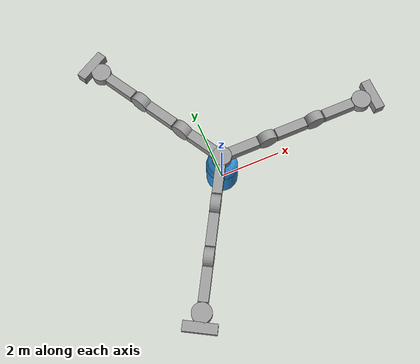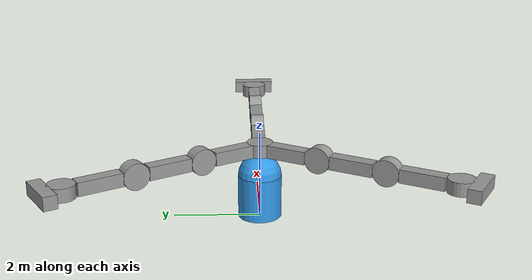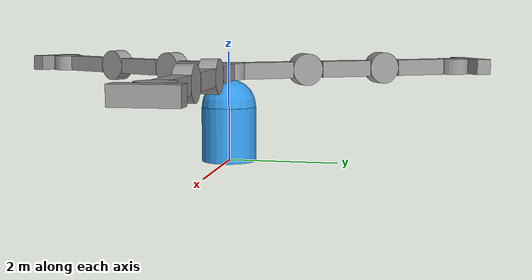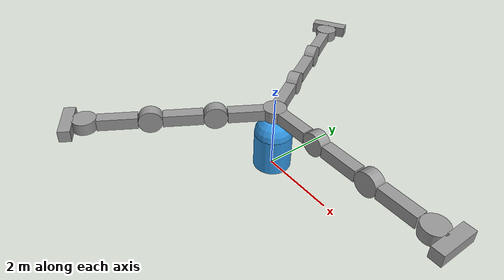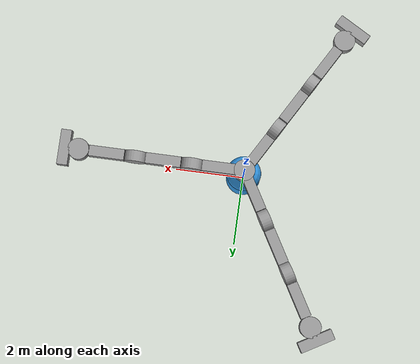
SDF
<?xml version='1.0'?>
<sdf version='1.6'>
  <model name='MR_bell_imu'>
    <link name='CORE1'>
      <pose frame=''>-0 -0 0.5 -0 -0 -0</pose>
      <inertial>
        <mass>1</mass>
        <inertia>
          <ixx>0.145833</ixx>
          <ixy>0</ixy>
          <ixz>0</ixz>
          <iyy>0.145833</iyy>
          <iyz>0</iyz>
          <izz>0.125</izz>
        </inertia>
        <pose frame=''>0 0 0 0 -0 0</pose>
      </inertial>
      <self_collide>0</self_collide>
      <kinematic>0</kinematic>
      <gravity>1</gravity>
      <visual name='visual'>
        <pose frame=''>0 0 0 0 -0 0</pose>
        <geometry>
          <cylinder>
            <radius>0.5</radius>
            <length>1</length>
          </cylinder>
        </geometry>
        <material>
          <lighting>1</lighting>
          <script>
            <uri>file://media/materials/scripts/gazebo.material</uri>
            <name>Gazebo/Grey</name>
          </script>
          <ambient>0.2 0.6 0.9 1</ambient>
          <diffuse>0.7 0.7 0.7 1</diffuse>
          <specular>0.01 0.01 0.01 1</specular>
          <emissive>0 0 0 1</emissive>
          <shader type='vertex'>
            <normal_map>__default__</normal_map>
          </shader>
        </material>
        <cast_shadows>1</cast_shadows>
        <transparency>0</transparency>
      </visual>
      <collision name='collision'>
        <laser_retro>0</laser_retro>
        <max_contacts>10</max_contacts>
        <pose frame=''>0 0 0 0 -0 0</pose>
        <geometry>
          <cylinder>
            <radius>0.5</radius>
            <length>1</length>
          </cylinder>
        </geometry>
        <surface>
          <friction>
            <ode>
              <mu>1</mu>
              <mu2>1</mu2>
              <fdir1>0 0 0</fdir1>
              <slip1>0</slip1>
              <slip2>0</slip2>
            </ode>
            <torsional>
              <coefficient>1</coefficient>
              <patch_radius>0</patch_radius>
              <surface_radius>0</surface_radius>
              <use_patch_radius>1</use_patch_radius>
              <ode>
                <slip>0</slip>
              </ode>
            </torsional>
          </friction>
          <bounce>
            <restitution_coefficient>0</restitution_coefficient>
            <threshold>1e+06</threshold>
          </bounce>
          <contact>
            <collide_without_contact>0</collide_without_contact>
            <collide_without_contact_bitmask>1</collide_without_contact_bitmask>
            <collide_bitmask>1</collide_bitmask>
            <ode>
              <soft_cfm>0</soft_cfm>
              <soft_erp>0.2</soft_erp>
              <kp>1e+13</kp>
              <kd>1</kd>
              <max_vel>0.01</max_vel>
              <min_depth>0</min_depth>
            </ode>
            <bullet>
              <split_impulse>1</split_impulse>
              <split_impulse_penetration_threshold>-0.01</split_impulse_penetration_threshold>
              <soft_cfm>0</soft_cfm>
              <soft_erp>0.2</soft_erp>
              <kp>1e+13</kp>
              <kd>1</kd>
            </bullet>
          </contact>
        </surface>
      </collision>
    </link>
    <link name='A1'>
      <pose frame=''>0.7 0.012999 1.64987 -0 -0 -0</pose>
      <inertial>
        <mass>1</mass>
        <inertia>
          <ixx>0.166667</ixx>
          <ixy>0</ixy>
          <ixz>0</ixz>
          <iyy>0.166667</iyy>
          <iyz>0</iyz>
          <izz>0.166667</izz>
        </inertia>
        <pose frame=''>0 0 0 0 -0 0</pose>
      </inertial>
      <self_collide>1</self_collide>
      <kinematic>0</kinematic>
      <gravity>1</gravity>
      <visual name='visual_0'>
        <pose frame=''>0 0 0 0 -0 0</pose>
        <geometry>
          <box>
            <size>1 0.3 0.3</size>
          </box>
        </geometry>
        <material>
          <lighting>1</lighting>
          <script>
            <uri>file://media/materials/scripts/gazebo.material</uri>
            <name>Gazebo/Grey</name>
          </script>
          <ambient>1 1 1 1</ambient>
          <diffuse>0.7 0.7 0.7 1</diffuse>
          <specular>0.01 0.01 0.01 1</specular>
          <emissive>0 0 0 1</emissive>
          <shader type='vertex'>
            <normal_map>__default__</normal_map>
          </shader>
        </material>
        <cast_shadows>1</cast_shadows>
        <transparency>0</transparency>
      </visual>
      <collision name='collision'>
        <laser_retro>0</laser_retro>
        <max_contacts>10</max_contacts>
        <pose frame=''>0 0 0 0 -0 0</pose>
        <geometry>
          <box>
            <size>1 0.3 0.3</size>
          </box>
        </geometry>
        <surface>
          <friction>
            <ode>
              <mu>1</mu>
              <mu2>1</mu2>
              <fdir1>0 0 0</fdir1>
              <slip1>0</slip1>
              <slip2>0</slip2>
            </ode>
            <torsional>
              <coefficient>1</coefficient>
              <patch_radius>0</patch_radius>
              <surface_radius>0</surface_radius>
              <use_patch_radius>1</use_patch_radius>
              <ode>
                <slip>0</slip>
              </ode>
            </torsional>
          </friction>
          <bounce>
            <restitution_coefficient>0</restitution_coefficient>
            <threshold>1e+06</threshold>
          </bounce>
          <contact>
            <collide_without_contact>0</collide_without_contact>
            <collide_without_contact_bitmask>1</collide_without_contact_bitmask>
            <collide_bitmask>1</collide_bitmask>
            <ode>
              <soft_cfm>0</soft_cfm>
              <soft_erp>0.2</soft_erp>
              <kp>1e+13</kp>
              <kd>1</kd>
              <max_vel>0.01</max_vel>
              <min_depth>0</min_depth>
            </ode>
            <bullet>
              <split_impulse>1</split_impulse>
              <split_impulse_penetration_threshold>-0.01</split_impulse_penetration_threshold>
              <soft_cfm>0</soft_cfm>
              <soft_erp>0.2</soft_erp>
              <kp>1e+13</kp>
              <kd>1</kd>
            </bullet>
          </contact>
        </surface>
      </collision>
    </link>
    <link name='A2'>
      <pose frame=''>2.3 0.012999 1.64987 -0 -0 -0</pose>
      <inertial>
        <mass>1</mass>
        <inertia>
          <ixx>0.166667</ixx>
          <ixy>0</ixy>
          <ixz>0</ixz>
          <iyy>0.166667</iyy>
          <iyz>0</iyz>
          <izz>0.166667</izz>
        </inertia>
        <pose frame=''>0 0 0 0 -0 0</pose>
      </inertial>
      <self_collide>1</self_collide>
      <kinematic>0</kinematic>
      <gravity>1</gravity>
      <visual name='visual_0'>
        <pose frame=''>0 0 0 0 -0 0</pose>
        <geometry>
          <box>
            <size>1 0.3 0.3</size>
          </box>
        </geometry>
        <material>
          <lighting>1</lighting>
          <script>
            <uri>file://media/materials/scripts/gazebo.material</uri>
            <name>Gazebo/Grey</name>
          </script>
          <ambient>1 1 1 1</ambient>
          <diffuse>0.7 0.7 0.7 1</diffuse>
          <specular>0.01 0.01 0.01 1</specular>
          <emissive>0 0 0 1</emissive>
          <shader type='vertex'>
            <normal_map>__default__</normal_map>
          </shader>
        </material>
        <cast_shadows>1</cast_shadows>
        <transparency>0</transparency>
      </visual>
      <collision name='collision'>
        <laser_retro>0</laser_retro>
        <max_contacts>10</max_contacts>
        <pose frame=''>0 0 0 0 -0 0</pose>
        <geometry>
          <box>
            <size>1 0.3 0.3</size>
          </box>
        </geometry>
        <surface>
          <friction>
            <ode>
              <mu>1</mu>
              <mu2>1</mu2>
              <fdir1>0 0 0</fdir1>
              <slip1>0</slip1>
              <slip2>0</slip2>
            </ode>
            <torsional>
              <coefficient>1</coefficient>
              <patch_radius>0</patch_radius>
              <surface_radius>0</surface_radius>
              <use_patch_radius>1</use_patch_radius>
              <ode>
                <slip>0</slip>
              </ode>
            </torsional>
          </friction>
          <bounce>
            <restitution_coefficient>0</restitution_coefficient>
            <threshold>1e+06</threshold>
          </bounce>
          <contact>
            <collide_without_contact>0</collide_without_contact>
            <collide_without_contact_bitmask>1</collide_without_contact_bitmask>
            <collide_bitmask>1</collide_bitmask>
            <ode>
              <soft_cfm>0</soft_cfm>
              <soft_erp>0.2</soft_erp>
              <kp>1e+13</kp>
              <kd>1</kd>
              <max_vel>0.01</max_vel>
              <min_depth>0</min_depth>
            </ode>
            <bullet>
              <split_impulse>1</split_impulse>
              <split_impulse_penetration_threshold>-0.01</split_impulse_penetration_threshold>
              <soft_cfm>0</soft_cfm>
              <soft_erp>0.2</soft_erp>
              <kp>1e+13</kp>
              <kd>1</kd>
            </bullet>
          </contact>
        </surface>
      </collision>
    </link>
    <link name='A3'>
      <pose frame=''>3.9 0.012999 1.64987 -0 -0 -0</pose>
      <inertial>
        <mass>1</mass>
        <inertia>
          <ixx>0.166667</ixx>
          <ixy>0</ixy>
          <ixz>0</ixz>
          <iyy>0.166667</iyy>
          <iyz>0</iyz>
          <izz>0.166667</izz>
        </inertia>
        <pose frame=''>0 0 0 0 -0 0</pose>
      </inertial>
      <self_collide>1</self_collide>
      <kinematic>0</kinematic>
      <gravity>1</gravity>
      <visual name='visual'>
        <pose frame=''>0 0 0 0 -0 0</pose>
        <geometry>
          <box>
            <size>1 0.3 0.3</size>
          </box>
        </geometry>
        <material>
          <lighting>1</lighting>
          <script>
            <uri>file://media/materials/scripts/gazebo.material</uri>
            <name>Gazebo/Grey</name>
          </script>
          <ambient>1 1 1 1</ambient>
          <diffuse>0.7 0.7 0.7 1</diffuse>
          <specular>0.01 0.01 0.01 1</specular>
          <emissive>0 0 0 1</emissive>
          <shader type='vertex'>
            <normal_map>__default__</normal_map>
          </shader>
        </material>
        <cast_shadows>1</cast_shadows>
        <transparency>0</transparency>
      </visual>
      <collision name='collision'>
        <laser_retro>0</laser_retro>
        <max_contacts>10</max_contacts>
        <pose frame=''>0 0 0 0 -0 0</pose>
        <geometry>
          <box>
            <size>1 0.3 0.3</size>
          </box>
        </geometry>
        <surface>
          <friction>
            <ode>
              <mu>1</mu>
              <mu2>1</mu2>
              <fdir1>0 0 0</fdir1>
              <slip1>0</slip1>
              <slip2>0</slip2>
            </ode>
            <torsional>
              <coefficient>1</coefficient>
              <patch_radius>0</patch_radius>
              <surface_radius>0</surface_radius>
              <use_patch_radius>1</use_patch_radius>
              <ode>
                <slip>0</slip>
              </ode>
            </torsional>
          </friction>
          <bounce>
            <restitution_coefficient>0</restitution_coefficient>
            <threshold>1e+06</threshold>
          </bounce>
          <contact>
            <collide_without_contact>0</collide_without_contact>
            <collide_without_contact_bitmask>1</collide_without_contact_bitmask>
            <collide_bitmask>1</collide_bitmask>
            <ode>
              <soft_cfm>0</soft_cfm>
              <soft_erp>0.2</soft_erp>
              <kp>1e+13</kp>
              <kd>1</kd>
              <max_vel>0.01</max_vel>
              <min_depth>0</min_depth>
            </ode>
            <bullet>
              <split_impulse>1</split_impulse>
              <split_impulse_penetration_threshold>-0.01</split_impulse_penetration_threshold>
              <soft_cfm>0</soft_cfm>
              <soft_erp>0.2</soft_erp>
              <kp>1e+13</kp>
              <kd>1</kd>
            </bullet>
          </contact>
        </surface>
      </collision>
    </link>
    <link name='A4'>
      <pose frame=''>5.1 0.013001 1.64987 0 -0 1.57079</pose>
      <inertial>
        <mass>1</mass>
        <inertia>
          <ixx>0.166667</ixx>
          <ixy>0</ixy>
          <ixz>0</ixz>
          <iyy>0.166667</iyy>
          <iyz>0</iyz>
          <izz>0.166667</izz>
        </inertia>
        <pose frame=''>0 0 0 0 -0 0</pose>
      </inertial>
      <self_collide>1</self_collide>
      <kinematic>0</kinematic>
      <gravity>1</gravity>
      <visual name='visual'>
        <pose frame=''>0 0 0 0 -0 0</pose>
        <geometry>
          <box>
            <size>1 0.3 0.3</size>
          </box>
        </geometry>
        <material>
          <lighting>1</lighting>
          <script>
            <uri>file://media/materials/scripts/gazebo.material</uri>
            <name>Gazebo/Grey</name>
          </script>
          <ambient>1 1 1 1</ambient>
          <diffuse>0.7 0.7 0.7 1</diffuse>
          <specular>0.01 0.01 0.01 1</specular>
          <emissive>0 0 0 1</emissive>
          <shader type='vertex'>
            <normal_map>__default__</normal_map>
          </shader>
        </material>
        <cast_shadows>1</cast_shadows>
        <transparency>0</transparency>
      </visual>
      <collision name='collision'>
        <laser_retro>0</laser_retro>
        <max_contacts>10</max_contacts>
        <pose frame=''>0 0 0 0 -0 0</pose>
        <geometry>
          <box>
            <size>1 0.3 0.3</size>
          </box>
        </geometry>
        <surface>
          <friction>
            <ode>
              <mu>1</mu>
              <mu2>1</mu2>
              <fdir1>0 0 0</fdir1>
              <slip1>0</slip1>
              <slip2>0</slip2>
            </ode>
            <torsional>
              <coefficient>1</coefficient>
              <patch_radius>0</patch_radius>
              <surface_radius>0</surface_radius>
              <use_patch_radius>1</use_patch_radius>
              <ode>
                <slip>0</slip>
              </ode>
            </torsional>
          </friction>
          <bounce>
            <restitution_coefficient>0</restitution_coefficient>
            <threshold>1e+06</threshold>
          </bounce>
          <contact>
            <collide_without_contact>0</collide_without_contact>
            <collide_without_contact_bitmask>1</collide_without_contact_bitmask>
            <collide_bitmask>1</collide_bitmask>
            <ode>
              <soft_cfm>0</soft_cfm>
              <soft_erp>0.2</soft_erp>
              <kp>1e+13</kp>
              <kd>1</kd>
              <max_vel>0.01</max_vel>
              <min_depth>0</min_depth>
            </ode>
            <bullet>
              <split_impulse>1</split_impulse>
              <split_impulse_penetration_threshold>-0.01</split_impulse_penetration_threshold>
              <soft_cfm>0</soft_cfm>
              <soft_erp>0.2</soft_erp>
              <kp>1e+13</kp>
              <kd>1</kd>
            </bullet>
          </contact>
        </surface>
      </collision>
    </link>
    <link name='B1'>
      <pose frame=''>-0.35 -0.593211 1.64987 0 -0 1.04719</pose>
      <inertial>
        <mass>1</mass>
        <inertia>
          <ixx>0.166667</ixx>
          <ixy>0</ixy>
          <ixz>0</ixz>
          <iyy>0.166667</iyy>
          <iyz>0</iyz>
          <izz>0.166667</izz>
        </inertia>
        <pose frame=''>0 0 0 0 -0 0</pose>
      </inertial>
      <self_collide>1</self_collide>
      <kinematic>0</kinematic>
      <gravity>1</gravity>
      <visual name='visual'>
        <pose frame=''>0 0 0 0 -0 0</pose>
        <geometry>
          <box>
            <size>1 0.3 0.3</size>
          </box>
        </geometry>
        <material>
          <lighting>1</lighting>
          <script>
            <uri>file://media/materials/scripts/gazebo.material</uri>
            <name>Gazebo/Grey</name>
          </script>
          <ambient>1 1 1 1</ambient>
          <diffuse>0.7 0.7 0.7 1</diffuse>
          <specular>0.01 0.01 0.01 1</specular>
          <emissive>0 0 0 1</emissive>
          <shader type='vertex'>
            <normal_map>__default__</normal_map>
          </shader>
        </material>
        <cast_shadows>1</cast_shadows>
        <transparency>0</transparency>
      </visual>
      <collision name='collision'>
        <laser_retro>0</laser_retro>
        <max_contacts>10</max_contacts>
        <pose frame=''>0 0 0 0 -0 0</pose>
        <geometry>
          <box>
            <size>1 0.3 0.3</size>
          </box>
        </geometry>
        <surface>
          <friction>
            <ode>
              <mu>1</mu>
              <mu2>1</mu2>
              <fdir1>0 0 0</fdir1>
              <slip1>0</slip1>
              <slip2>0</slip2>
            </ode>
            <torsional>
              <coefficient>1</coefficient>
              <patch_radius>0</patch_radius>
              <surface_radius>0</surface_radius>
              <use_patch_radius>1</use_patch_radius>
              <ode>
                <slip>0</slip>
              </ode>
            </torsional>
          </friction>
          <bounce>
            <restitution_coefficient>0</restitution_coefficient>
            <threshold>1e+06</threshold>
          </bounce>
          <contact>
            <collide_without_contact>0</collide_without_contact>
            <collide_without_contact_bitmask>1</collide_without_contact_bitmask>
            <collide_bitmask>1</collide_bitmask>
            <ode>
              <soft_cfm>0</soft_cfm>
              <soft_erp>0.2</soft_erp>
              <kp>1e+13</kp>
              <kd>1</kd>
              <max_vel>0.01</max_vel>
              <min_depth>0</min_depth>
            </ode>
            <bullet>
              <split_impulse>1</split_impulse>
              <split_impulse_penetration_threshold>-0.01</split_impulse_penetration_threshold>
              <soft_cfm>0</soft_cfm>
              <soft_erp>0.2</soft_erp>
              <kp>1e+13</kp>
              <kd>1</kd>
            </bullet>
          </contact>
        </surface>
      </collision>
    </link>
    <link name='B2'>
      <pose frame=''>-1.15001 -1.97885 1.64987 0 -0 1.04719</pose>
      <inertial>
        <mass>1</mass>
        <inertia>
          <ixx>0.166667</ixx>
          <ixy>0</ixy>
          <ixz>0</ixz>
          <iyy>0.166667</iyy>
          <iyz>0</iyz>
          <izz>0.166667</izz>
        </inertia>
        <pose frame=''>0 0 0 0 -0 0</pose>
      </inertial>
      <self_collide>1</self_collide>
      <kinematic>0</kinematic>
      <gravity>1</gravity>
      <visual name='visual'>
        <pose frame=''>0 0 0 0 -0 0</pose>
        <geometry>
          <box>
            <size>1 0.3 0.3</size>
          </box>
        </geometry>
        <material>
          <lighting>1</lighting>
          <script>
            <uri>file://media/materials/scripts/gazebo.material</uri>
            <name>Gazebo/Grey</name>
          </script>
          <ambient>1 1 1 1</ambient>
          <diffuse>0.7 0.7 0.7 1</diffuse>
          <specular>0.01 0.01 0.01 1</specular>
          <emissive>0 0 0 1</emissive>
          <shader type='vertex'>
            <normal_map>__default__</normal_map>
          </shader>
        </material>
        <cast_shadows>1</cast_shadows>
        <transparency>0</transparency>
      </visual>
      <collision name='collision'>
        <laser_retro>0</laser_retro>
        <max_contacts>10</max_contacts>
        <pose frame=''>0 0 0 0 -0 0</pose>
        <geometry>
          <box>
            <size>1 0.3 0.3</size>
          </box>
        </geometry>
        <surface>
          <friction>
            <ode>
              <mu>1</mu>
              <mu2>1</mu2>
              <fdir1>0 0 0</fdir1>
              <slip1>0</slip1>
              <slip2>0</slip2>
            </ode>
            <torsional>
              <coefficient>1</coefficient>
              <patch_radius>0</patch_radius>
              <surface_radius>0</surface_radius>
              <use_patch_radius>1</use_patch_radius>
              <ode>
                <slip>0</slip>
              </ode>
            </torsional>
          </friction>
          <bounce>
            <restitution_coefficient>0</restitution_coefficient>
            <threshold>1e+06</threshold>
          </bounce>
          <contact>
            <collide_without_contact>0</collide_without_contact>
            <collide_without_contact_bitmask>1</collide_without_contact_bitmask>
            <collide_bitmask>1</collide_bitmask>
            <ode>
              <soft_cfm>0</soft_cfm>
              <soft_erp>0.2</soft_erp>
              <kp>1e+13</kp>
              <kd>1</kd>
              <max_vel>0.01</max_vel>
              <min_depth>0</min_depth>
            </ode>
            <bullet>
              <split_impulse>1</split_impulse>
              <split_impulse_penetration_threshold>-0.01</split_impulse_penetration_threshold>
              <soft_cfm>0</soft_cfm>
              <soft_erp>0.2</soft_erp>
              <kp>1e+13</kp>
              <kd>1</kd>
            </bullet>
          </contact>
        </surface>
      </collision>
    </link>
    <link name='B3'>
      <pose frame=''>-1.95002 -3.36448 1.64987 0 -0 1.04719</pose>
      <inertial>
        <mass>1</mass>
        <inertia>
          <ixx>0.166667</ixx>
          <ixy>0</ixy>
          <ixz>0</ixz>
          <iyy>0.166667</iyy>
          <iyz>0</iyz>
          <izz>0.166667</izz>
        </inertia>
        <pose frame=''>0 0 0 0 -0 0</pose>
      </inertial>
      <self_collide>1</self_collide>
      <kinematic>0</kinematic>
      <gravity>1</gravity>
      <visual name='visual'>
        <pose frame=''>0 0 0 0 -0 0</pose>
        <geometry>
          <box>
            <size>1 0.3 0.3</size>
          </box>
        </geometry>
        <material>
          <lighting>1</lighting>
          <script>
            <uri>file://media/materials/scripts/gazebo.material</uri>
            <name>Gazebo/Grey</name>
          </script>
          <ambient>1 1 1 1</ambient>
          <diffuse>0.7 0.7 0.7 1</diffuse>
          <specular>0.01 0.01 0.01 1</specular>
          <emissive>0 0 0 1</emissive>
          <shader type='vertex'>
            <normal_map>__default__</normal_map>
          </shader>
        </material>
        <cast_shadows>1</cast_shadows>
        <transparency>0</transparency>
      </visual>
      <collision name='collision'>
        <laser_retro>0</laser_retro>
        <max_contacts>10</max_contacts>
        <pose frame=''>0 0 0 0 -0 0</pose>
        <geometry>
          <box>
            <size>1 0.3 0.3</size>
          </box>
        </geometry>
        <surface>
          <friction>
            <ode>
              <mu>1</mu>
              <mu2>1</mu2>
              <fdir1>0 0 0</fdir1>
              <slip1>0</slip1>
              <slip2>0</slip2>
            </ode>
            <torsional>
              <coefficient>1</coefficient>
              <patch_radius>0</patch_radius>
              <surface_radius>0</surface_radius>
              <use_patch_radius>1</use_patch_radius>
              <ode>
                <slip>0</slip>
              </ode>
            </torsional>
          </friction>
          <bounce>
            <restitution_coefficient>0</restitution_coefficient>
            <threshold>1e+06</threshold>
          </bounce>
          <contact>
            <collide_without_contact>0</collide_without_contact>
            <collide_without_contact_bitmask>1</collide_without_contact_bitmask>
            <collide_bitmask>1</collide_bitmask>
            <ode>
              <soft_cfm>0</soft_cfm>
              <soft_erp>0.2</soft_erp>
              <kp>1e+13</kp>
              <kd>1</kd>
              <max_vel>0.01</max_vel>
              <min_depth>0</min_depth>
            </ode>
            <bullet>
              <split_impulse>1</split_impulse>
              <split_impulse_penetration_threshold>-0.01</split_impulse_penetration_threshold>
              <soft_cfm>0</soft_cfm>
              <soft_erp>0.2</soft_erp>
              <kp>1e+13</kp>
              <kd>1</kd>
            </bullet>
          </contact>
        </surface>
      </collision>
    </link>
    <link name='B4'>
      <pose frame=''>-2.55003 -4.40371 1.64987 -0 -0 -0.523598</pose>
      <inertial>
        <mass>1</mass>
        <inertia>
          <ixx>0.166667</ixx>
          <ixy>0</ixy>
          <ixz>0</ixz>
          <iyy>0.166667</iyy>
          <iyz>0</iyz>
          <izz>0.166667</izz>
        </inertia>
        <pose frame=''>0 0 0 0 -0 0</pose>
      </inertial>
      <self_collide>1</self_collide>
      <kinematic>0</kinematic>
      <gravity>1</gravity>
      <visual name='visual_0'>
        <pose frame=''>0 0 0 0 -0 0</pose>
        <geometry>
          <box>
            <size>1 0.3 0.3</size>
          </box>
        </geometry>
        <material>
          <lighting>1</lighting>
          <script>
            <uri>file://media/materials/scripts/gazebo.material</uri>
            <name>Gazebo/Grey</name>
          </script>
          <ambient>1 1 1 1</ambient>
          <diffuse>0.7 0.7 0.7 1</diffuse>
          <specular>0.01 0.01 0.01 1</specular>
          <emissive>0 0 0 1</emissive>
          <shader type='vertex'>
            <normal_map>__default__</normal_map>
          </shader>
        </material>
        <cast_shadows>1</cast_shadows>
        <transparency>0</transparency>
      </visual>
      <collision name='collision'>
        <laser_retro>0</laser_retro>
        <max_contacts>10</max_contacts>
        <pose frame=''>0 0 0 0 -0 0</pose>
        <geometry>
          <box>
            <size>1 0.3 0.3</size>
          </box>
        </geometry>
        <surface>
          <friction>
            <ode>
              <mu>1</mu>
              <mu2>1</mu2>
              <fdir1>0 0 0</fdir1>
              <slip1>0</slip1>
              <slip2>0</slip2>
            </ode>
            <torsional>
              <coefficient>1</coefficient>
              <patch_radius>0</patch_radius>
              <surface_radius>0</surface_radius>
              <use_patch_radius>1</use_patch_radius>
              <ode>
                <slip>0</slip>
              </ode>
            </torsional>
          </friction>
          <bounce>
            <restitution_coefficient>0</restitution_coefficient>
            <threshold>1e+06</threshold>
          </bounce>
          <contact>
            <collide_without_contact>0</collide_without_contact>
            <collide_without_contact_bitmask>1</collide_without_contact_bitmask>
            <collide_bitmask>1</collide_bitmask>
            <ode>
              <soft_cfm>0</soft_cfm>
              <soft_erp>0.2</soft_erp>
              <kp>1e+13</kp>
              <kd>1</kd>
              <max_vel>0.01</max_vel>
              <min_depth>0</min_depth>
            </ode>
            <bullet>
              <split_impulse>1</split_impulse>
              <split_impulse_penetration_threshold>-0.01</split_impulse_penetration_threshold>
              <soft_cfm>0</soft_cfm>
              <soft_erp>0.2</soft_erp>
              <kp>1e+13</kp>
              <kd>1</kd>
            </bullet>
          </contact>
        </surface>
      </collision>
    </link>
    <link name='C1'>
      <pose frame=''>-0.35 0.619209 1.64987 0 0 -1.04719</pose>
      <inertial>
        <mass>1</mass>
        <inertia>
          <ixx>0.166667</ixx>
          <ixy>0</ixy>
          <ixz>0</ixz>
          <iyy>0.166667</iyy>
          <iyz>0</iyz>
          <izz>0.166667</izz>
        </inertia>
        <pose frame=''>0 0 0 0 -0 0</pose>
      </inertial>
      <self_collide>1</self_collide>
      <kinematic>0</kinematic>
      <gravity>1</gravity>
      <visual name='visual_0'>
        <pose frame=''>0 0 0 0 -0 0</pose>
        <geometry>
          <box>
            <size>1 0.3 0.3</size>
          </box>
        </geometry>
        <material>
          <lighting>1</lighting>
          <script>
            <uri>file://media/materials/scripts/gazebo.material</uri>
            <name>Gazebo/Grey</name>
          </script>
          <ambient>1 1 1 1</ambient>
          <diffuse>0.7 0.7 0.7 1</diffuse>
          <specular>0.01 0.01 0.01 1</specular>
          <emissive>0 0 0 1</emissive>
          <shader type='vertex'>
            <normal_map>__default__</normal_map>
          </shader>
        </material>
        <cast_shadows>1</cast_shadows>
        <transparency>0</transparency>
      </visual>
      <collision name='collision'>
        <laser_retro>0</laser_retro>
        <max_contacts>10</max_contacts>
        <pose frame=''>0 0 0 0 -0 0</pose>
        <geometry>
          <box>
            <size>1 0.3 0.3</size>
          </box>
        </geometry>
        <surface>
          <friction>
            <ode>
              <mu>1</mu>
              <mu2>1</mu2>
              <fdir1>0 0 0</fdir1>
              <slip1>0</slip1>
              <slip2>0</slip2>
            </ode>
            <torsional>
              <coefficient>1</coefficient>
              <patch_radius>0</patch_radius>
              <surface_radius>0</surface_radius>
              <use_patch_radius>1</use_patch_radius>
              <ode>
                <slip>0</slip>
              </ode>
            </torsional>
          </friction>
          <bounce>
            <restitution_coefficient>0</restitution_coefficient>
            <threshold>1e+06</threshold>
          </bounce>
          <contact>
            <collide_without_contact>0</collide_without_contact>
            <collide_without_contact_bitmask>1</collide_without_contact_bitmask>
            <collide_bitmask>1</collide_bitmask>
            <ode>
              <soft_cfm>0</soft_cfm>
              <soft_erp>0.2</soft_erp>
              <kp>1e+13</kp>
              <kd>1</kd>
              <max_vel>0.01</max_vel>
              <min_depth>0</min_depth>
            </ode>
            <bullet>
              <split_impulse>1</split_impulse>
              <split_impulse_penetration_threshold>-0.01</split_impulse_penetration_threshold>
              <soft_cfm>0</soft_cfm>
              <soft_erp>0.2</soft_erp>
              <kp>1e+13</kp>
              <kd>1</kd>
            </bullet>
          </contact>
        </surface>
      </collision>
    </link>
    <link name='C2'>
      <pose frame=''>-1.15001 2.00484 1.64987 0 0 -1.04719</pose>
      <inertial>
        <mass>1</mass>
        <inertia>
          <ixx>0.166667</ixx>
          <ixy>0</ixy>
          <ixz>0</ixz>
          <iyy>0.166667</iyy>
          <iyz>0</iyz>
          <izz>0.166667</izz>
        </inertia>
        <pose frame=''>0 0 0 0 -0 0</pose>
      </inertial>
      <self_collide>1</self_collide>
      <kinematic>0</kinematic>
      <gravity>1</gravity>
      <visual name='visual_0'>
        <pose frame=''>0 0 0 0 -0 0</pose>
        <geometry>
          <box>
            <size>1 0.3 0.3</size>
          </box>
        </geometry>
        <material>
          <lighting>1</lighting>
          <script>
            <uri>file://media/materials/scripts/gazebo.material</uri>
            <name>Gazebo/Grey</name>
          </script>
          <ambient>1 1 1 1</ambient>
          <diffuse>0.7 0.7 0.7 1</diffuse>
          <specular>0.01 0.01 0.01 1</specular>
          <emissive>0 0 0 1</emissive>
          <shader type='vertex'>
            <normal_map>__default__</normal_map>
          </shader>
        </material>
        <cast_shadows>1</cast_shadows>
        <transparency>0</transparency>
      </visual>
      <collision name='collision'>
        <laser_retro>0</laser_retro>
        <max_contacts>10</max_contacts>
        <pose frame=''>0 0 0 0 -0 0</pose>
        <geometry>
          <box>
            <size>1 0.3 0.3</size>
          </box>
        </geometry>
        <surface>
          <friction>
            <ode>
              <mu>1</mu>
              <mu2>1</mu2>
              <fdir1>0 0 0</fdir1>
              <slip1>0</slip1>
              <slip2>0</slip2>
            </ode>
            <torsional>
              <coefficient>1</coefficient>
              <patch_radius>0</patch_radius>
              <surface_radius>0</surface_radius>
              <use_patch_radius>1</use_patch_radius>
              <ode>
                <slip>0</slip>
              </ode>
            </torsional>
          </friction>
          <bounce>
            <restitution_coefficient>0</restitution_coefficient>
            <threshold>1e+06</threshold>
          </bounce>
          <contact>
            <collide_without_contact>0</collide_without_contact>
            <collide_without_contact_bitmask>1</collide_without_contact_bitmask>
            <collide_bitmask>1</collide_bitmask>
            <ode>
              <soft_cfm>0</soft_cfm>
              <soft_erp>0.2</soft_erp>
              <kp>1e+13</kp>
              <kd>1</kd>
              <max_vel>0.01</max_vel>
              <min_depth>0</min_depth>
            </ode>
            <bullet>
              <split_impulse>1</split_impulse>
              <split_impulse_penetration_threshold>-0.01</split_impulse_penetration_threshold>
              <soft_cfm>0</soft_cfm>
              <soft_erp>0.2</soft_erp>
              <kp>1e+13</kp>
              <kd>1</kd>
            </bullet>
          </contact>
        </surface>
      </collision>
    </link>
    <link name='C3'>
      <pose frame=''>-1.95002 3.39048 1.64987 0 0 -1.04719</pose>
      <inertial>
        <mass>1</mass>
        <inertia>
          <ixx>0.166667</ixx>
          <ixy>0</ixy>
          <ixz>0</ixz>
          <iyy>0.166667</iyy>
          <iyz>0</iyz>
          <izz>0.166667</izz>
        </inertia>
        <pose frame=''>0 0 0 0 -0 0</pose>
      </inertial>
      <self_collide>1</self_collide>
      <kinematic>0</kinematic>
      <gravity>1</gravity>
      <visual name='visual_0'>
        <pose frame=''>0 0 0 0 -0 0</pose>
        <geometry>
          <box>
            <size>1 0.3 0.3</size>
          </box>
        </geometry>
        <material>
          <lighting>1</lighting>
          <script>
            <uri>file://media/materials/scripts/gazebo.material</uri>
            <name>Gazebo/Grey</name>
          </script>
          <ambient>1 1 1 1</ambient>
          <diffuse>0.7 0.7 0.7 1</diffuse>
          <specular>0.01 0.01 0.01 1</specular>
          <emissive>0 0 0 1</emissive>
          <shader type='vertex'>
            <normal_map>__default__</normal_map>
          </shader>
        </material>
        <cast_shadows>1</cast_shadows>
        <transparency>0</transparency>
      </visual>
      <collision name='collision'>
        <laser_retro>0</laser_retro>
        <max_contacts>10</max_contacts>
        <pose frame=''>0 0 0 0 -0 0</pose>
        <geometry>
          <box>
            <size>1 0.3 0.3</size>
          </box>
        </geometry>
        <surface>
          <friction>
            <ode>
              <mu>1</mu>
              <mu2>1</mu2>
              <fdir1>0 0 0</fdir1>
              <slip1>0</slip1>
              <slip2>0</slip2>
            </ode>
            <torsional>
              <coefficient>1</coefficient>
              <patch_radius>0</patch_radius>
              <surface_radius>0</surface_radius>
              <use_patch_radius>1</use_patch_radius>
              <ode>
                <slip>0</slip>
              </ode>
            </torsional>
          </friction>
          <bounce>
            <restitution_coefficient>0</restitution_coefficient>
            <threshold>1e+06</threshold>
          </bounce>
          <contact>
            <collide_without_contact>0</collide_without_contact>
            <collide_without_contact_bitmask>1</collide_without_contact_bitmask>
            <collide_bitmask>1</collide_bitmask>
            <ode>
              <soft_cfm>0</soft_cfm>
              <soft_erp>0.2</soft_erp>
              <kp>1e+13</kp>
              <kd>1</kd>
              <max_vel>0.01</max_vel>
              <min_depth>0</min_depth>
            </ode>
            <bullet>
              <split_impulse>1</split_impulse>
              <split_impulse_penetration_threshold>-0.01</split_impulse_penetration_threshold>
              <soft_cfm>0</soft_cfm>
              <soft_erp>0.2</soft_erp>
              <kp>1e+13</kp>
              <kd>1</kd>
            </bullet>
          </contact>
        </surface>
      </collision>
    </link>
    <link name='C4'>
      <pose frame=''>-2.55003 4.4297 1.64987 0 -0 0.523598</pose>
      <inertial>
        <mass>1</mass>
        <inertia>
          <ixx>0.166667</ixx>
          <ixy>0</ixy>
          <ixz>0</ixz>
          <iyy>0.166667</iyy>
          <iyz>0</iyz>
          <izz>0.166667</izz>
        </inertia>
        <pose frame=''>0 0 0 0 -0 0</pose>
      </inertial>
      <self_collide>1</self_collide>
      <kinematic>0</kinematic>
      <gravity>1</gravity>
      <visual name='visual'>
        <pose frame=''>0 0 0 0 -0 0</pose>
        <geometry>
          <box>
            <size>1 0.3 0.3</size>
          </box>
        </geometry>
        <material>
          <lighting>1</lighting>
          <script>
            <uri>file://media/materials/scripts/gazebo.material</uri>
            <name>Gazebo/Grey</name>
          </script>
          <ambient>1 1 1 1</ambient>
          <diffuse>0.7 0.7 0.7 1</diffuse>
          <specular>0.01 0.01 0.01 1</specular>
          <emissive>0 0 0 1</emissive>
          <shader type='vertex'>
            <normal_map>__default__</normal_map>
          </shader>
        </material>
        <cast_shadows>1</cast_shadows>
        <transparency>0</transparency>
      </visual>
      <collision name='collision'>
        <laser_retro>0</laser_retro>
        <max_contacts>10</max_contacts>
        <pose frame=''>0 0 0 0 -0 0</pose>
        <geometry>
          <box>
            <size>1 0.3 0.3</size>
          </box>
        </geometry>
        <surface>
          <friction>
            <ode>
              <mu>1</mu>
              <mu2>1</mu2>
              <fdir1>0 0 0</fdir1>
              <slip1>0</slip1>
              <slip2>0</slip2>
            </ode>
            <torsional>
              <coefficient>1</coefficient>
              <patch_radius>0</patch_radius>
              <surface_radius>0</surface_radius>
              <use_patch_radius>1</use_patch_radius>
              <ode>
                <slip>0</slip>
              </ode>
            </torsional>
          </friction>
          <bounce>
            <restitution_coefficient>0</restitution_coefficient>
            <threshold>1e+06</threshold>
          </bounce>
          <contact>
            <collide_without_contact>0</collide_without_contact>
            <collide_without_contact_bitmask>1</collide_without_contact_bitmask>
            <collide_bitmask>1</collide_bitmask>
            <ode>
              <soft_cfm>0</soft_cfm>
              <soft_erp>0.2</soft_erp>
              <kp>1e+13</kp>
              <kd>1</kd>
              <max_vel>0.01</max_vel>
              <min_depth>0</min_depth>
            </ode>
            <bullet>
              <split_impulse>1</split_impulse>
              <split_impulse_penetration_threshold>-0.01</split_impulse_penetration_threshold>
              <soft_cfm>0</soft_cfm>
              <soft_erp>0.2</soft_erp>
              <kp>1e+13</kp>
              <kd>1</kd>
            </bullet>
          </contact>
        </surface>
      </collision>
    </link>
    <link name='CORE2'>
      <pose frame=''>0 3e-06 1 -0 -0 -0</pose>
      <inertial>
        <mass>1</mass>
        <inertia>
          <ixx>0.1</ixx>
          <ixy>0</ixy>
          <ixz>0</ixz>
          <iyy>0.1</iyy>
          <iyz>0</iyz>
          <izz>0.1</izz>
        </inertia>
        <pose frame=''>0 0 0 0 -0 0</pose>
      </inertial>
      <self_collide>0</self_collide>
      <kinematic>0</kinematic>
      <visual name='visual'>
        <pose frame=''>0 0 0 0 -0 0</pose>
        <geometry>
          <sphere>
            <radius>0.5</radius>
          </sphere>
        </geometry>
        <material>
          <lighting>1</lighting>
          <script>
            <uri>file://media/materials/scripts/gazebo.material</uri>
            <name>Gazebo/Grey</name>
          </script>
          <ambient>0.2 0.6 0.9 1</ambient>
          <diffuse>0.7 0.7 0.7 1</diffuse>
          <specular>0.01 0.01 0.01 1</specular>
          <emissive>0 0 0 1</emissive>
          <shader type='vertex'>
            <normal_map>__default__</normal_map>
          </shader>
        </material>
        <cast_shadows>1</cast_shadows>
        <transparency>0</transparency>
      </visual>
      <collision name='collision'>
        <laser_retro>0</laser_retro>
        <max_contacts>10</max_contacts>
        <pose frame=''>0 0 0 0 -0 0</pose>
        <geometry>
          <sphere>
            <radius>0.5</radius>
          </sphere>
        </geometry>
        <surface>
          <friction>
            <ode>
              <mu>1</mu>
              <mu2>1</mu2>
              <fdir1>0 0 0</fdir1>
              <slip1>0</slip1>
              <slip2>0</slip2>
            </ode>
            <torsional>
              <coefficient>1</coefficient>
              <patch_radius>0</patch_radius>
              <surface_radius>0</surface_radius>
              <use_patch_radius>1</use_patch_radius>
              <ode>
                <slip>0</slip>
              </ode>
            </torsional>
          </friction>
          <bounce>
            <restitution_coefficient>0</restitution_coefficient>
            <threshold>1e+06</threshold>
          </bounce>
          <contact>
            <collide_without_contact>0</collide_without_contact>
            <collide_without_contact_bitmask>1</collide_without_contact_bitmask>
            <collide_bitmask>1</collide_bitmask>
            <ode>
              <soft_cfm>0</soft_cfm>
              <soft_erp>0.2</soft_erp>
              <kp>1e+13</kp>
              <kd>1</kd>
              <max_vel>0.01</max_vel>
              <min_depth>0</min_depth>
            </ode>
            <bullet>
              <split_impulse>1</split_impulse>
              <split_impulse_penetration_threshold>-0.01</split_impulse_penetration_threshold>
              <soft_cfm>0</soft_cfm>
              <soft_erp>0.2</soft_erp>
              <kp>1e+13</kp>
              <kd>1</kd>
            </bullet>
          </contact>
        </surface>
      </collision>
    </link>
    <link name='M0'>
      <pose frame=''>-0 3e-06 1.65 -0 -0 -0</pose>
      <inertial>
        <mass>1</mass>
        <inertia>
          <ixx>0.145833</ixx>
          <ixy>0</ixy>
          <ixz>0</ixz>
          <iyy>0.145833</iyy>
          <iyz>0</iyz>
          <izz>0.125</izz>
        </inertia>
        <pose frame=''>0 0 0 0 -0 0</pose>
      </inertial>
      <self_collide>0</self_collide>
      <kinematic>0</kinematic>
      <visual name='visual'>
        <pose frame=''>0 0 0 0 -0 0</pose>
        <geometry>
          <cylinder>
            <radius>0.3</radius>
            <length>0.3</length>
          </cylinder>
        </geometry>
        <material>
          <lighting>1</lighting>
          <script>
            <uri>file://media/materials/scripts/gazebo.material</uri>
            <name>Gazebo/Grey</name>
          </script>
          <ambient>0 0 0 1</ambient>
          <diffuse>0.7 0.7 0.7 1</diffuse>
          <specular>0.01 0.01 0.01 1</specular>
          <emissive>0 0 0 1</emissive>
          <shader type='vertex'>
            <normal_map>__default__</normal_map>
          </shader>
        </material>
        <cast_shadows>1</cast_shadows>
        <transparency>0</transparency>
      </visual>
      <collision name='collision'>
        <laser_retro>0</laser_retro>
        <max_contacts>10</max_contacts>
        <pose frame=''>0 0 0 0 -0 0</pose>
        <geometry>
          <cylinder>
            <radius>0.3</radius>
            <length>0.3</length>
          </cylinder>
        </geometry>
        <surface>
          <friction>
            <ode>
              <mu>1</mu>
              <mu2>1</mu2>
              <fdir1>0 0 0</fdir1>
              <slip1>0</slip1>
              <slip2>0</slip2>
            </ode>
            <torsional>
              <coefficient>1</coefficient>
              <patch_radius>0</patch_radius>
              <surface_radius>0</surface_radius>
              <use_patch_radius>1</use_patch_radius>
              <ode>
                <slip>0</slip>
              </ode>
            </torsional>
          </friction>
          <bounce>
            <restitution_coefficient>0</restitution_coefficient>
            <threshold>1e+06</threshold>
          </bounce>
          <contact>
            <collide_without_contact>0</collide_without_contact>
            <collide_without_contact_bitmask>1</collide_without_contact_bitmask>
            <collide_bitmask>1</collide_bitmask>
            <ode>
              <soft_cfm>0</soft_cfm>
              <soft_erp>0.2</soft_erp>
              <kp>1e+13</kp>
              <kd>1</kd>
              <max_vel>0.01</max_vel>
              <min_depth>0</min_depth>
            </ode>
            <bullet>
              <split_impulse>1</split_impulse>
              <split_impulse_penetration_threshold>-0.01</split_impulse_penetration_threshold>
              <soft_cfm>0</soft_cfm>
              <soft_erp>0.2</soft_erp>
              <kp>1e+13</kp>
              <kd>1</kd>
            </bullet>
          </contact>
        </surface>
      </collision>
    </link>
    <link name='MA-1'>
      <pose frame=''>1.5 0.012999 1.64987 1.57 -0 0</pose>
      <inertial>
        <mass>1</mass>
        <inertia>
          <ixx>0.145833</ixx>
          <ixy>0</ixy>
          <ixz>0</ixz>
          <iyy>0.145833</iyy>
          <iyz>0</iyz>
          <izz>0.125</izz>
        </inertia>
        <pose frame=''>0 0 0 0 -0 0</pose>
      </inertial>
      <self_collide>0</self_collide>
      <kinematic>0</kinematic>
      <visual name='visual_0'>
        <pose frame=''>0 0 0 0 -0 0</pose>
        <geometry>
          <cylinder>
            <radius>0.3</radius>
            <length>0.3</length>
          </cylinder>
        </geometry>
        <material>
          <lighting>1</lighting>
          <script>
            <uri>file://media/materials/scripts/gazebo.material</uri>
            <name>Gazebo/Grey</name>
          </script>
          <ambient>0 0 0 1</ambient>
          <diffuse>0.7 0.7 0.7 1</diffuse>
          <specular>0.01 0.01 0.01 1</specular>
          <emissive>0 0 0 1</emissive>
          <shader type='vertex'>
            <normal_map>__default__</normal_map>
          </shader>
        </material>
        <cast_shadows>1</cast_shadows>
        <transparency>0</transparency>
      </visual>
      <collision name='collision'>
        <laser_retro>0</laser_retro>
        <max_contacts>10</max_contacts>
        <pose frame=''>0 0 0 0 -0 0</pose>
        <geometry>
          <cylinder>
            <radius>0.3</radius>
            <length>0.3</length>
          </cylinder>
        </geometry>
        <surface>
          <friction>
            <ode>
              <mu>1</mu>
              <mu2>1</mu2>
              <fdir1>0 0 0</fdir1>
              <slip1>0</slip1>
              <slip2>0</slip2>
            </ode>
            <torsional>
              <coefficient>1</coefficient>
              <patch_radius>0</patch_radius>
              <surface_radius>0</surface_radius>
              <use_patch_radius>1</use_patch_radius>
              <ode>
                <slip>0</slip>
              </ode>
            </torsional>
          </friction>
          <bounce>
            <restitution_coefficient>0</restitution_coefficient>
            <threshold>1e+06</threshold>
          </bounce>
          <contact>
            <collide_without_contact>0</collide_without_contact>
            <collide_without_contact_bitmask>1</collide_without_contact_bitmask>
            <collide_bitmask>1</collide_bitmask>
            <ode>
              <soft_cfm>0</soft_cfm>
              <soft_erp>0.2</soft_erp>
              <kp>1e+13</kp>
              <kd>1</kd>
              <max_vel>0.01</max_vel>
              <min_depth>0</min_depth>
            </ode>
            <bullet>
              <split_impulse>1</split_impulse>
              <split_impulse_penetration_threshold>-0.01</split_impulse_penetration_threshold>
              <soft_cfm>0</soft_cfm>
              <soft_erp>0.2</soft_erp>
              <kp>1e+13</kp>
              <kd>1</kd>
            </bullet>
          </contact>
        </surface>
      </collision>
    </link>
    <link name='MA-2'>
      <pose frame=''>3.1 0.012999 1.64987 1.57 -0 0</pose>
      <inertial>
        <mass>1</mass>
        <inertia>
          <ixx>0.145833</ixx>
          <ixy>0</ixy>
          <ixz>0</ixz>
          <iyy>0.145833</iyy>
          <iyz>0</iyz>
          <izz>0.125</izz>
        </inertia>
        <pose frame=''>0 0 0 0 -0 0</pose>
      </inertial>
      <self_collide>0</self_collide>
      <kinematic>0</kinematic>
      <visual name='visual'>
        <pose frame=''>0 0 0 0 -0 0</pose>
        <geometry>
          <cylinder>
            <radius>0.3</radius>
            <length>0.3</length>
          </cylinder>
        </geometry>
        <material>
          <lighting>1</lighting>
          <script>
            <uri>file://media/materials/scripts/gazebo.material</uri>
            <name>Gazebo/Grey</name>
          </script>
          <ambient>0 0 0 1</ambient>
          <diffuse>0.7 0.7 0.7 1</diffuse>
          <specular>0.01 0.01 0.01 1</specular>
          <emissive>0 0 0 1</emissive>
          <shader type='vertex'>
            <normal_map>__default__</normal_map>
          </shader>
        </material>
        <cast_shadows>1</cast_shadows>
        <transparency>0</transparency>
      </visual>
      <collision name='collision'>
        <laser_retro>0</laser_retro>
        <max_contacts>10</max_contacts>
        <pose frame=''>0 0 0 0 -0 0</pose>
        <geometry>
          <cylinder>
            <radius>0.3</radius>
            <length>0.3</length>
          </cylinder>
        </geometry>
        <surface>
          <friction>
            <ode>
              <mu>1</mu>
              <mu2>1</mu2>
              <fdir1>0 0 0</fdir1>
              <slip1>0</slip1>
              <slip2>0</slip2>
            </ode>
            <torsional>
              <coefficient>1</coefficient>
              <patch_radius>0</patch_radius>
              <surface_radius>0</surface_radius>
              <use_patch_radius>1</use_patch_radius>
              <ode>
                <slip>0</slip>
              </ode>
            </torsional>
          </friction>
          <bounce>
            <restitution_coefficient>0</restitution_coefficient>
            <threshold>1e+06</threshold>
          </bounce>
          <contact>
            <collide_without_contact>0</collide_without_contact>
            <collide_without_contact_bitmask>1</collide_without_contact_bitmask>
            <collide_bitmask>1</collide_bitmask>
            <ode>
              <soft_cfm>0</soft_cfm>
              <soft_erp>0.2</soft_erp>
              <kp>1e+13</kp>
              <kd>1</kd>
              <max_vel>0.01</max_vel>
              <min_depth>0</min_depth>
            </ode>
            <bullet>
              <split_impulse>1</split_impulse>
              <split_impulse_penetration_threshold>-0.01</split_impulse_penetration_threshold>
              <soft_cfm>0</soft_cfm>
              <soft_erp>0.2</soft_erp>
              <kp>1e+13</kp>
              <kd>1</kd>
            </bullet>
          </contact>
        </surface>
      </collision>
    </link>
    <link name='MA-3'>
      <pose frame=''>4.7 0.012998 1.64987 -0 -0 -0</pose>
      <inertial>
        <mass>1</mass>
        <inertia>
          <ixx>0.145833</ixx>
          <ixy>0</ixy>
          <ixz>0</ixz>
          <iyy>0.145833</iyy>
          <iyz>0</iyz>
          <izz>0.125</izz>
        </inertia>
        <pose frame=''>0 0 0 0 -0 0</pose>
      </inertial>
      <self_collide>0</self_collide>
      <kinematic>0</kinematic>
      <visual name='visual'>
        <pose frame=''>0 0 0 0 -0 0</pose>
        <geometry>
          <cylinder>
            <radius>0.3</radius>
            <length>0.3</length>
          </cylinder>
        </geometry>
        <material>
          <lighting>1</lighting>
          <script>
            <uri>file://media/materials/scripts/gazebo.material</uri>
            <name>Gazebo/Grey</name>
          </script>
          <ambient>0 0 0 1</ambient>
          <diffuse>0.7 0.7 0.7 1</diffuse>
          <specular>0.01 0.01 0.01 1</specular>
          <emissive>0 0 0 1</emissive>
          <shader type='vertex'>
            <normal_map>__default__</normal_map>
          </shader>
        </material>
        <cast_shadows>1</cast_shadows>
        <transparency>0</transparency>
      </visual>
      <collision name='collision'>
        <laser_retro>0</laser_retro>
        <max_contacts>10</max_contacts>
        <pose frame=''>0 0 0 0 -0 0</pose>
        <geometry>
          <cylinder>
            <radius>0.3</radius>
            <length>0.3</length>
          </cylinder>
        </geometry>
        <surface>
          <friction>
            <ode>
              <mu>1</mu>
              <mu2>1</mu2>
              <fdir1>0 0 0</fdir1>
              <slip1>0</slip1>
              <slip2>0</slip2>
            </ode>
            <torsional>
              <coefficient>1</coefficient>
              <patch_radius>0</patch_radius>
              <surface_radius>0</surface_radius>
              <use_patch_radius>1</use_patch_radius>
              <ode>
                <slip>0</slip>
              </ode>
            </torsional>
          </friction>
          <bounce>
            <restitution_coefficient>0</restitution_coefficient>
            <threshold>1e+06</threshold>
          </bounce>
          <contact>
            <collide_without_contact>0</collide_without_contact>
            <collide_without_contact_bitmask>1</collide_without_contact_bitmask>
            <collide_bitmask>1</collide_bitmask>
            <ode>
              <soft_cfm>0</soft_cfm>
              <soft_erp>0.2</soft_erp>
              <kp>1e+13</kp>
              <kd>1</kd>
              <max_vel>0.01</max_vel>
              <min_depth>0</min_depth>
            </ode>
            <bullet>
              <split_impulse>1</split_impulse>
              <split_impulse_penetration_threshold>-0.01</split_impulse_penetration_threshold>
              <soft_cfm>0</soft_cfm>
              <soft_erp>0.2</soft_erp>
              <kp>1e+13</kp>
              <kd>1</kd>
            </bullet>
          </contact>
        </surface>
      </collision>
    </link>
    <link name='MB-4'>
      <pose frame=''>-0.750005 -1.28603 1.64987 1.57 -0 1.04719</pose>
      <inertial>
        <mass>1</mass>
        <inertia>
          <ixx>0.145833</ixx>
          <ixy>0</ixy>
          <ixz>0</ixz>
          <iyy>0.145833</iyy>
          <iyz>0</iyz>
          <izz>0.125</izz>
        </inertia>
        <pose frame=''>0 0 0 0 -0 0</pose>
      </inertial>
      <self_collide>0</self_collide>
      <kinematic>0</kinematic>
      <visual name='visual_0'>
        <pose frame=''>0 0 0 0 -0 0</pose>
        <geometry>
          <cylinder>
            <radius>0.3</radius>
            <length>0.3</length>
          </cylinder>
        </geometry>
        <material>
          <lighting>1</lighting>
          <script>
            <uri>file://media/materials/scripts/gazebo.material</uri>
            <name>Gazebo/Grey</name>
          </script>
          <ambient>0 0 0 1</ambient>
          <diffuse>0.7 0.7 0.7 1</diffuse>
          <specular>0.01 0.01 0.01 1</specular>
          <emissive>0 0 0 1</emissive>
          <shader type='vertex'>
            <normal_map>__default__</normal_map>
          </shader>
        </material>
        <cast_shadows>1</cast_shadows>
        <transparency>0</transparency>
      </visual>
      <collision name='collision'>
        <laser_retro>0</laser_retro>
        <max_contacts>10</max_contacts>
        <pose frame=''>0 0 0 0 -0 0</pose>
        <geometry>
          <cylinder>
            <radius>0.3</radius>
            <length>0.3</length>
          </cylinder>
        </geometry>
        <surface>
          <friction>
            <ode>
              <mu>1</mu>
              <mu2>1</mu2>
              <fdir1>0 0 0</fdir1>
              <slip1>0</slip1>
              <slip2>0</slip2>
            </ode>
            <torsional>
              <coefficient>1</coefficient>
              <patch_radius>0</patch_radius>
              <surface_radius>0</surface_radius>
              <use_patch_radius>1</use_patch_radius>
              <ode>
                <slip>0</slip>
              </ode>
            </torsional>
          </friction>
          <bounce>
            <restitution_coefficient>0</restitution_coefficient>
            <threshold>1e+06</threshold>
          </bounce>
          <contact>
            <collide_without_contact>0</collide_without_contact>
            <collide_without_contact_bitmask>1</collide_without_contact_bitmask>
            <collide_bitmask>1</collide_bitmask>
            <ode>
              <soft_cfm>0</soft_cfm>
              <soft_erp>0.2</soft_erp>
              <kp>1e+13</kp>
              <kd>1</kd>
              <max_vel>0.01</max_vel>
              <min_depth>0</min_depth>
            </ode>
            <bullet>
              <split_impulse>1</split_impulse>
              <split_impulse_penetration_threshold>-0.01</split_impulse_penetration_threshold>
              <soft_cfm>0</soft_cfm>
              <soft_erp>0.2</soft_erp>
              <kp>1e+13</kp>
              <kd>1</kd>
            </bullet>
          </contact>
        </surface>
      </collision>
    </link>
    <link name='MB-5'>
      <pose frame=''>-1.55002 -2.67166 1.64987 1.57 -0 1.04719</pose>
      <inertial>
        <mass>1</mass>
        <inertia>
          <ixx>0.145833</ixx>
          <ixy>0</ixy>
          <ixz>0</ixz>
          <iyy>0.145833</iyy>
          <iyz>0</iyz>
          <izz>0.125</izz>
        </inertia>
        <pose frame=''>0 0 0 0 -0 0</pose>
      </inertial>
      <self_collide>0</self_collide>
      <kinematic>0</kinematic>
      <visual name='visual_0'>
        <pose frame=''>0 0 0 0 -0 0</pose>
        <geometry>
          <cylinder>
            <radius>0.3</radius>
            <length>0.3</length>
          </cylinder>
        </geometry>
        <material>
          <lighting>1</lighting>
          <script>
            <uri>file://media/materials/scripts/gazebo.material</uri>
            <name>Gazebo/Grey</name>
          </script>
          <ambient>0 0 0 1</ambient>
          <diffuse>0.7 0.7 0.7 1</diffuse>
          <specular>0.01 0.01 0.01 1</specular>
          <emissive>0 0 0 1</emissive>
          <shader type='vertex'>
            <normal_map>__default__</normal_map>
          </shader>
        </material>
        <cast_shadows>1</cast_shadows>
        <transparency>0</transparency>
      </visual>
      <collision name='collision'>
        <laser_retro>0</laser_retro>
        <max_contacts>10</max_contacts>
        <pose frame=''>0 0 0 0 -0 0</pose>
        <geometry>
          <cylinder>
            <radius>0.3</radius>
            <length>0.3</length>
          </cylinder>
        </geometry>
        <surface>
          <friction>
            <ode>
              <mu>1</mu>
              <mu2>1</mu2>
              <fdir1>0 0 0</fdir1>
              <slip1>0</slip1>
              <slip2>0</slip2>
            </ode>
            <torsional>
              <coefficient>1</coefficient>
              <patch_radius>0</patch_radius>
              <surface_radius>0</surface_radius>
              <use_patch_radius>1</use_patch_radius>
              <ode>
                <slip>0</slip>
              </ode>
            </torsional>
          </friction>
          <bounce>
            <restitution_coefficient>0</restitution_coefficient>
            <threshold>1e+06</threshold>
          </bounce>
          <contact>
            <collide_without_contact>0</collide_without_contact>
            <collide_without_contact_bitmask>1</collide_without_contact_bitmask>
            <collide_bitmask>1</collide_bitmask>
            <ode>
              <soft_cfm>0</soft_cfm>
              <soft_erp>0.2</soft_erp>
              <kp>1e+13</kp>
              <kd>1</kd>
              <max_vel>0.01</max_vel>
              <min_depth>0</min_depth>
            </ode>
            <bullet>
              <split_impulse>1</split_impulse>
              <split_impulse_penetration_threshold>-0.01</split_impulse_penetration_threshold>
              <soft_cfm>0</soft_cfm>
              <soft_erp>0.2</soft_erp>
              <kp>1e+13</kp>
              <kd>1</kd>
            </bullet>
          </contact>
        </surface>
      </collision>
    </link>
    <link name='MB-6'>
      <pose frame=''>-2.35003 -4.0573 1.64987 0 -0 1.04719</pose>
      <inertial>
        <mass>1</mass>
        <inertia>
          <ixx>0.145833</ixx>
          <ixy>0</ixy>
          <ixz>0</ixz>
          <iyy>0.145833</iyy>
          <iyz>0</iyz>
          <izz>0.125</izz>
        </inertia>
        <pose frame=''>0 0 0 0 -0 0</pose>
      </inertial>
      <self_collide>0</self_collide>
      <kinematic>0</kinematic>
      <visual name='visual'>
        <pose frame=''>0 0 0 0 -0 0</pose>
        <geometry>
          <cylinder>
            <radius>0.3</radius>
            <length>0.3</length>
          </cylinder>
        </geometry>
        <material>
          <lighting>1</lighting>
          <script>
            <uri>file://media/materials/scripts/gazebo.material</uri>
            <name>Gazebo/Grey</name>
          </script>
          <ambient>0 0 0 1</ambient>
          <diffuse>0.7 0.7 0.7 1</diffuse>
          <specular>0.01 0.01 0.01 1</specular>
          <emissive>0 0 0 1</emissive>
          <shader type='vertex'>
            <normal_map>__default__</normal_map>
          </shader>
        </material>
        <cast_shadows>1</cast_shadows>
        <transparency>0</transparency>
      </visual>
      <collision name='collision'>
        <laser_retro>0</laser_retro>
        <max_contacts>10</max_contacts>
        <pose frame=''>0 0 0 0 -0 0</pose>
        <geometry>
          <cylinder>
            <radius>0.3</radius>
            <length>0.3</length>
          </cylinder>
        </geometry>
        <surface>
          <friction>
            <ode>
              <mu>1</mu>
              <mu2>1</mu2>
              <fdir1>0 0 0</fdir1>
              <slip1>0</slip1>
              <slip2>0</slip2>
            </ode>
            <torsional>
              <coefficient>1</coefficient>
              <patch_radius>0</patch_radius>
              <surface_radius>0</surface_radius>
              <use_patch_radius>1</use_patch_radius>
              <ode>
                <slip>0</slip>
              </ode>
            </torsional>
          </friction>
          <bounce>
            <restitution_coefficient>0</restitution_coefficient>
            <threshold>1e+06</threshold>
          </bounce>
          <contact>
            <collide_without_contact>0</collide_without_contact>
            <collide_without_contact_bitmask>1</collide_without_contact_bitmask>
            <collide_bitmask>1</collide_bitmask>
            <ode>
              <soft_cfm>0</soft_cfm>
              <soft_erp>0.2</soft_erp>
              <kp>1e+13</kp>
              <kd>1</kd>
              <max_vel>0.01</max_vel>
              <min_depth>0</min_depth>
            </ode>
            <bullet>
              <split_impulse>1</split_impulse>
              <split_impulse_penetration_threshold>-0.01</split_impulse_penetration_threshold>
              <soft_cfm>0</soft_cfm>
              <soft_erp>0.2</soft_erp>
              <kp>1e+13</kp>
              <kd>1</kd>
            </bullet>
          </contact>
        </surface>
      </collision>
    </link>
    <link name='MC-7'>
      <pose frame=''>-0.750005 1.31203 1.64987 1.57 -0 -1.04719</pose>
      <inertial>
        <mass>1</mass>
        <inertia>
          <ixx>0.145833</ixx>
          <ixy>0</ixy>
          <ixz>0</ixz>
          <iyy>0.145833</iyy>
          <iyz>0</iyz>
          <izz>0.125</izz>
        </inertia>
        <pose frame=''>0 0 0 0 -0 0</pose>
      </inertial>
      <self_collide>0</self_collide>
      <kinematic>0</kinematic>
      <visual name='visual_0'>
        <pose frame=''>0 0 0 0 -0 0</pose>
        <geometry>
          <cylinder>
            <radius>0.3</radius>
            <length>0.3</length>
          </cylinder>
        </geometry>
        <material>
          <lighting>1</lighting>
          <script>
            <uri>file://media/materials/scripts/gazebo.material</uri>
            <name>Gazebo/Grey</name>
          </script>
          <ambient>0 0 0 1</ambient>
          <diffuse>0.7 0.7 0.7 1</diffuse>
          <specular>0.01 0.01 0.01 1</specular>
          <emissive>0 0 0 1</emissive>
          <shader type='vertex'>
            <normal_map>__default__</normal_map>
          </shader>
        </material>
        <cast_shadows>1</cast_shadows>
        <transparency>0</transparency>
      </visual>
      <collision name='collision'>
        <laser_retro>0</laser_retro>
        <max_contacts>10</max_contacts>
        <pose frame=''>0 0 0 0 -0 0</pose>
        <geometry>
          <cylinder>
            <radius>0.3</radius>
            <length>0.3</length>
          </cylinder>
        </geometry>
        <surface>
          <friction>
            <ode>
              <mu>1</mu>
              <mu2>1</mu2>
              <fdir1>0 0 0</fdir1>
              <slip1>0</slip1>
              <slip2>0</slip2>
            </ode>
            <torsional>
              <coefficient>1</coefficient>
              <patch_radius>0</patch_radius>
              <surface_radius>0</surface_radius>
              <use_patch_radius>1</use_patch_radius>
              <ode>
                <slip>0</slip>
              </ode>
            </torsional>
          </friction>
          <bounce>
            <restitution_coefficient>0</restitution_coefficient>
            <threshold>1e+06</threshold>
          </bounce>
          <contact>
            <collide_without_contact>0</collide_without_contact>
            <collide_without_contact_bitmask>1</collide_without_contact_bitmask>
            <collide_bitmask>1</collide_bitmask>
            <ode>
              <soft_cfm>0</soft_cfm>
              <soft_erp>0.2</soft_erp>
              <kp>1e+13</kp>
              <kd>1</kd>
              <max_vel>0.01</max_vel>
              <min_depth>0</min_depth>
            </ode>
            <bullet>
              <split_impulse>1</split_impulse>
              <split_impulse_penetration_threshold>-0.01</split_impulse_penetration_threshold>
              <soft_cfm>0</soft_cfm>
              <soft_erp>0.2</soft_erp>
              <kp>1e+13</kp>
              <kd>1</kd>
            </bullet>
          </contact>
        </surface>
      </collision>
    </link>
    <link name='MC-8'>
      <pose frame=''>-1.55002 2.69766 1.64987 1.57 -0 -1.04719</pose>
      <inertial>
        <mass>1</mass>
        <inertia>
          <ixx>0.145833</ixx>
          <ixy>0</ixy>
          <ixz>0</ixz>
          <iyy>0.145833</iyy>
          <iyz>0</iyz>
          <izz>0.125</izz>
        </inertia>
        <pose frame=''>0 0 0 0 -0 0</pose>
      </inertial>
      <self_collide>0</self_collide>
      <kinematic>0</kinematic>
      <visual name='visual_0'>
        <pose frame=''>0 0 0 0 -0 0</pose>
        <geometry>
          <cylinder>
            <radius>0.3</radius>
            <length>0.3</length>
          </cylinder>
        </geometry>
        <material>
          <lighting>1</lighting>
          <script>
            <uri>file://media/materials/scripts/gazebo.material</uri>
            <name>Gazebo/Grey</name>
          </script>
          <ambient>0 0 0 1</ambient>
          <diffuse>0.7 0.7 0.7 1</diffuse>
          <specular>0.01 0.01 0.01 1</specular>
          <emissive>0 0 0 1</emissive>
          <shader type='vertex'>
            <normal_map>__default__</normal_map>
          </shader>
        </material>
        <cast_shadows>1</cast_shadows>
        <transparency>0</transparency>
      </visual>
      <collision name='collision'>
        <laser_retro>0</laser_retro>
        <max_contacts>10</max_contacts>
        <pose frame=''>0 0 0 0 -0 0</pose>
        <geometry>
          <cylinder>
            <radius>0.3</radius>
            <length>0.3</length>
          </cylinder>
        </geometry>
        <surface>
          <friction>
            <ode>
              <mu>1</mu>
              <mu2>1</mu2>
              <fdir1>0 0 0</fdir1>
              <slip1>0</slip1>
              <slip2>0</slip2>
            </ode>
            <torsional>
              <coefficient>1</coefficient>
              <patch_radius>0</patch_radius>
              <surface_radius>0</surface_radius>
              <use_patch_radius>1</use_patch_radius>
              <ode>
                <slip>0</slip>
              </ode>
            </torsional>
          </friction>
          <bounce>
            <restitution_coefficient>0</restitution_coefficient>
            <threshold>1e+06</threshold>
          </bounce>
          <contact>
            <collide_without_contact>0</collide_without_contact>
            <collide_without_contact_bitmask>1</collide_without_contact_bitmask>
            <collide_bitmask>1</collide_bitmask>
            <ode>
              <soft_cfm>0</soft_cfm>
              <soft_erp>0.2</soft_erp>
              <kp>1e+13</kp>
              <kd>1</kd>
              <max_vel>0.01</max_vel>
              <min_depth>0</min_depth>
            </ode>
            <bullet>
              <split_impulse>1</split_impulse>
              <split_impulse_penetration_threshold>-0.01</split_impulse_penetration_threshold>
              <soft_cfm>0</soft_cfm>
              <soft_erp>0.2</soft_erp>
              <kp>1e+13</kp>
              <kd>1</kd>
            </bullet>
          </contact>
        </surface>
      </collision>
    </link>
    <link name='MC-9'>
      <pose frame=''>-2.35003 4.08329 1.64987 0 0 -1.04719</pose>
      <inertial>
        <mass>1</mass>
        <inertia>
          <ixx>0.145833</ixx>
          <ixy>0</ixy>
          <ixz>0</ixz>
          <iyy>0.145833</iyy>
          <iyz>0</iyz>
          <izz>0.125</izz>
        </inertia>
        <pose frame=''>0 0 0 0 -0 0</pose>
      </inertial>
      <self_collide>0</self_collide>
      <kinematic>0</kinematic>
      <visual name='visual'>
        <pose frame=''>0 0 0 0 -0 0</pose>
        <geometry>
          <cylinder>
            <radius>0.3</radius>
            <length>0.3</length>
          </cylinder>
        </geometry>
        <material>
          <lighting>1</lighting>
          <script>
            <uri>file://media/materials/scripts/gazebo.material</uri>
            <name>Gazebo/Grey</name>
          </script>
          <ambient>0 0 0 1</ambient>
          <diffuse>0.7 0.7 0.7 1</diffuse>
          <specular>0.01 0.01 0.01 1</specular>
          <emissive>0 0 0 1</emissive>
          <shader type='vertex'>
            <normal_map>__default__</normal_map>
          </shader>
        </material>
        <cast_shadows>1</cast_shadows>
        <transparency>0</transparency>
      </visual>
      <collision name='collision'>
        <laser_retro>0</laser_retro>
        <max_contacts>10</max_contacts>
        <pose frame=''>0 0 0 0 -0 0</pose>
        <geometry>
          <cylinder>
            <radius>0.3</radius>
            <length>0.3</length>
          </cylinder>
        </geometry>
        <surface>
          <friction>
            <ode>
              <mu>1</mu>
              <mu2>1</mu2>
              <fdir1>0 0 0</fdir1>
              <slip1>0</slip1>
              <slip2>0</slip2>
            </ode>
            <torsional>
              <coefficient>1</coefficient>
              <patch_radius>0</patch_radius>
              <surface_radius>0</surface_radius>
              <use_patch_radius>1</use_patch_radius>
              <ode>
                <slip>0</slip>
              </ode>
            </torsional>
          </friction>
          <bounce>
            <restitution_coefficient>0</restitution_coefficient>
            <threshold>1e+06</threshold>
          </bounce>
          <contact>
            <collide_without_contact>0</collide_without_contact>
            <collide_without_contact_bitmask>1</collide_without_contact_bitmask>
            <collide_bitmask>1</collide_bitmask>
            <ode>
              <soft_cfm>0</soft_cfm>
              <soft_erp>0.2</soft_erp>
              <kp>1e+13</kp>
              <kd>1</kd>
              <max_vel>0.01</max_vel>
              <min_depth>0</min_depth>
            </ode>
            <bullet>
              <split_impulse>1</split_impulse>
              <split_impulse_penetration_threshold>-0.01</split_impulse_penetration_threshold>
              <soft_cfm>0</soft_cfm>
              <soft_erp>0.2</soft_erp>
              <kp>1e+13</kp>
              <kd>1</kd>
            </bullet>
          </contact>
        </surface>
      </collision>
    </link>
    <link name='imu_link'>
      <pose frame=''>0 3e-06 1 0.002403 -0.000745 0.006526</pose>
      <inertial>
        <mass>1</mass>
        <inertia>
          <ixx>0.166667</ixx>
          <ixy>0</ixy>
          <ixz>0</ixz>
          <iyy>0.166667</iyy>
          <iyz>0</iyz>
          <izz>0.166667</izz>
        </inertia>
        <pose frame=''>0 0 0 0 -0 0</pose>
      </inertial>
      <self_collide>0</self_collide>
      <kinematic>0</kinematic>
      <visual name='visual'>
        <pose frame=''>0 0 0 0 -0 0</pose>
        <geometry>
          <box>
            <size>0.3 0.3 0.3</size>
          </box>
        </geometry>
        <material>
          <lighting>1</lighting>
          <script>
            <uri>file://media/materials/scripts/gazebo.material</uri>
            <name>Gazebo/Grey</name>
          </script>
          <ambient>0.3 0.3 0.3 1</ambient>
          <diffuse>0.7 0.7 0.7 1</diffuse>
          <specular>0.01 0.01 0.01 1</specular>
          <emissive>0 0 0 1</emissive>
          <shader type='vertex'>
            <normal_map>__default__</normal_map>
          </shader>
        </material>
        <cast_shadows>1</cast_shadows>
        <transparency>0</transparency>
      </visual>
      <collision name='collision'>
        <laser_retro>0</laser_retro>
        <max_contacts>10</max_contacts>
        <pose frame=''>0 0 0 0 -0 0</pose>
        <geometry>
          <box>
            <size>0.3 0.3 0.3</size>
          </box>
        </geometry>
        <surface>
          <friction>
            <ode>
              <mu>1</mu>
              <mu2>1</mu2>
              <fdir1>0 0 0</fdir1>
              <slip1>0</slip1>
              <slip2>0</slip2>
            </ode>
            <torsional>
              <coefficient>1</coefficient>
              <patch_radius>0</patch_radius>
              <surface_radius>0</surface_radius>
              <use_patch_radius>1</use_patch_radius>
              <ode>
                <slip>0</slip>
              </ode>
            </torsional>
          </friction>
          <bounce>
            <restitution_coefficient>0</restitution_coefficient>
            <threshold>1e+06</threshold>
          </bounce>
          <contact>
            <collide_without_contact>0</collide_without_contact>
            <collide_without_contact_bitmask>1</collide_without_contact_bitmask>
            <collide_bitmask>1</collide_bitmask>
            <ode>
              <soft_cfm>0</soft_cfm>
              <soft_erp>0.2</soft_erp>
              <kp>1e+13</kp>
              <kd>1</kd>
              <max_vel>0.01</max_vel>
              <min_depth>0</min_depth>
            </ode>
            <bullet>
              <split_impulse>1</split_impulse>
              <split_impulse_penetration_threshold>-0.01</split_impulse_penetration_threshold>
              <soft_cfm>0</soft_cfm>
              <soft_erp>0.2</soft_erp>
              <kp>1e+13</kp>
              <kd>1</kd>
            </bullet>
          </contact>
        </surface>
      </collision>
    </link>
    <joint name='F10' type='fixed'>
      <parent>MC-7</parent>
      <child>C2</child>
      <pose frame=''>0 0 0 0 -0 0</pose>
      <physics>
        <ode>
          <limit>
            <cfm>0</cfm>
            <erp>0.2</erp>
          </limit>
          <suspension>
            <cfm>0</cfm>
            <erp>0.2</erp>
          </suspension>
        </ode>
      </physics>
    </joint>
    <joint name='F11' type='fixed'>
      <parent>MC-8</parent>
      <child>C3</child>
      <pose frame=''>0 0 0 0 -0 0</pose>
      <physics>
        <ode>
          <limit>
            <cfm>0</cfm>
            <erp>0.2</erp>
          </limit>
          <suspension>
            <cfm>0</cfm>
            <erp>0.2</erp>
          </suspension>
        </ode>
      </physics>
    </joint>
    <joint name='F12' type='fixed'>
      <parent>MC-9</parent>
      <child>C4</child>
      <pose frame=''>0 0 0 0 -0 0</pose>
      <physics>
        <ode>
          <limit>
            <cfm>0</cfm>
            <erp>0.2</erp>
          </limit>
          <suspension>
            <cfm>0</cfm>
            <erp>0.2</erp>
          </suspension>
        </ode>
      </physics>
    </joint>
    <joint name='F1' type='fixed'>
      <parent>M0</parent>
      <child>A1</child>
      <pose frame=''>0 0 0 0 -0 0</pose>
      <physics>
        <ode>
          <limit>
            <cfm>0</cfm>
            <erp>0.2</erp>
          </limit>
          <suspension>
            <cfm>0</cfm>
            <erp>0.2</erp>
          </suspension>
        </ode>
      </physics>
    </joint>
    <joint name='F2' type='fixed'>
      <parent>MA-1</parent>
      <child>A2</child>
      <pose frame=''>0 0 0 0 -0 0</pose>
      <physics>
        <ode>
          <limit>
            <cfm>0</cfm>
            <erp>0.2</erp>
          </limit>
          <suspension>
            <cfm>0</cfm>
            <erp>0.2</erp>
          </suspension>
        </ode>
      </physics>
    </joint>
    <joint name='F3' type='fixed'>
      <parent>MA-2</parent>
      <child>A3</child>
      <pose frame=''>0 0 0 0 -0 0</pose>
      <physics>
        <ode>
          <limit>
            <cfm>0</cfm>
            <erp>0.2</erp>
          </limit>
          <suspension>
            <cfm>0</cfm>
            <erp>0.2</erp>
          </suspension>
        </ode>
      </physics>
    </joint>
    <joint name='F4' type='fixed'>
      <parent>MA-3</parent>
      <child>A4</child>
      <pose frame=''>0 0 0 0 -0 0</pose>
      <physics>
        <ode>
          <limit>
            <cfm>0</cfm>
            <erp>0.2</erp>
          </limit>
          <suspension>
            <cfm>0</cfm>
            <erp>0.2</erp>
          </suspension>
        </ode>
      </physics>
    </joint>
    <joint name='F5' type='fixed'>
      <parent>M0</parent>
      <child>B1</child>
      <pose frame=''>0 0 0 0 -0 0</pose>
      <physics>
        <ode>
          <limit>
            <cfm>0</cfm>
            <erp>0.2</erp>
          </limit>
          <suspension>
            <cfm>0</cfm>
            <erp>0.2</erp>
          </suspension>
        </ode>
      </physics>
    </joint>
    <joint name='F6' type='fixed'>
      <parent>MB-4</parent>
      <child>B2</child>
      <pose frame=''>0 0 0 0 -0 0</pose>
      <physics>
        <ode>
          <limit>
            <cfm>0</cfm>
            <erp>0.2</erp>
          </limit>
          <suspension>
            <cfm>0</cfm>
            <erp>0.2</erp>
          </suspension>
        </ode>
      </physics>
    </joint>
    <joint name='F7' type='fixed'>
      <parent>MB-5</parent>
      <child>B3</child>
      <pose frame=''>0 0 0 0 -0 0</pose>
      <physics>
        <ode>
          <limit>
            <cfm>0</cfm>
            <erp>0.2</erp>
          </limit>
          <suspension>
            <cfm>0</cfm>
            <erp>0.2</erp>
          </suspension>
        </ode>
      </physics>
    </joint>
    <joint name='F8' type='fixed'>
      <parent>MB-6</parent>
      <child>B4</child>
      <pose frame=''>0 0 0 0 -0 0</pose>
      <physics>
        <ode>
          <limit>
            <cfm>0</cfm>
            <erp>0.2</erp>
          </limit>
          <suspension>
            <cfm>0</cfm>
            <erp>0.2</erp>
          </suspension>
        </ode>
      </physics>
    </joint>
    <joint name='F9' type='fixed'>
      <parent>M0</parent>
      <child>C1</child>
      <pose frame=''>0 0 0 0 -0 0</pose>
      <physics>
        <ode>
          <limit>
            <cfm>0</cfm>
            <erp>0.2</erp>
          </limit>
          <suspension>
            <cfm>0</cfm>
            <erp>0.2</erp>
          </suspension>
        </ode>
      </physics>
    </joint>
    <joint name='FCORE' type='fixed'>
      <parent>CORE1</parent>
      <child>CORE2</child>
      <pose frame=''>0 0 0 0 -0 0</pose>
      <physics>
        <ode>
          <limit>
            <cfm>0</cfm>
            <erp>0.2</erp>
          </limit>
          <suspension>
            <cfm>0</cfm>
            <erp>0.2</erp>
          </suspension>
        </ode>
      </physics>
    </joint>
    <joint name='Y1' type='revolute'>
      <parent>A1</parent>
      <child>MA-1</child>
      <pose frame=''>0 0 0 0 -0 0</pose>
      <axis>
        <xyz>0 0 1</xyz>
        <use_parent_model_frame>0</use_parent_model_frame>
        <limit>
          <lower>-1.79769e+308</lower>
          <upper>1.79769e+308</upper>
          <effort>-1</effort>
          <velocity>-1</velocity>
        </limit>
        <dynamics>
          <spring_reference>0</spring_reference>
          <spring_stiffness>0</spring_stiffness>
          <damping>0</damping>
          <friction>0</friction>
        </dynamics>
      </axis>
      <physics>
        <ode>
          <limit>
            <cfm>0</cfm>
            <erp>0.2</erp>
          </limit>
          <suspension>
            <cfm>0</cfm>
            <erp>0.2</erp>
          </suspension>
        </ode>
      </physics>
    </joint>
    <joint name='Y2' type='revolute'>
      <parent>A2</parent>
      <child>MA-2</child>
      <pose frame=''>0 0 0 0 -0 0</pose>
      <axis>
        <xyz>0 0 1</xyz>
        <use_parent_model_frame>0</use_parent_model_frame>
        <limit>
          <lower>-1.79769e+308</lower>
          <upper>1.79769e+308</upper>
          <effort>-1</effort>
          <velocity>-1</velocity>
        </limit>
        <dynamics>
          <spring_reference>0</spring_reference>
          <spring_stiffness>0</spring_stiffness>
          <damping>0</damping>
          <friction>0</friction>
        </dynamics>
      </axis>
      <physics>
        <ode>
          <limit>
            <cfm>0</cfm>
            <erp>0.2</erp>
          </limit>
          <suspension>
            <cfm>0</cfm>
            <erp>0.2</erp>
          </suspension>
        </ode>
      </physics>
    </joint>
    <joint name='Y3' type='revolute'>
      <parent>A3</parent>
      <child>MA-3</child>
      <pose frame=''>0 0 0 0 -0 0</pose>
      <axis>
        <xyz>0 0 1</xyz>
        <use_parent_model_frame>0</use_parent_model_frame>
        <limit>
          <lower>-1.79769e+308</lower>
          <upper>1.79769e+308</upper>
          <effort>-1</effort>
          <velocity>-1</velocity>
        </limit>
        <dynamics>
          <spring_reference>0</spring_reference>
          <spring_stiffness>0</spring_stiffness>
          <damping>0</damping>
          <friction>0</friction>
        </dynamics>
      </axis>
      <physics>
        <ode>
          <limit>
            <cfm>0</cfm>
            <erp>0.2</erp>
          </limit>
          <suspension>
            <cfm>0</cfm>
            <erp>0.2</erp>
          </suspension>
        </ode>
      </physics>
    </joint>
    <joint name='Y4' type='revolute'>
      <parent>B1</parent>
      <child>MB-4</child>
      <pose frame=''>0 0 0 0 -0 0</pose>
      <axis>
        <xyz>0 0 1</xyz>
        <use_parent_model_frame>0</use_parent_model_frame>
        <limit>
          <lower>-1.79769e+308</lower>
          <upper>1.79769e+308</upper>
          <effort>-1</effort>
          <velocity>-1</velocity>
        </limit>
        <dynamics>
          <spring_reference>0</spring_reference>
          <spring_stiffness>0</spring_stiffness>
          <damping>0</damping>
          <friction>0</friction>
        </dynamics>
      </axis>
      <physics>
        <ode>
          <limit>
            <cfm>0</cfm>
            <erp>0.2</erp>
          </limit>
          <suspension>
            <cfm>0</cfm>
            <erp>0.2</erp>
          </suspension>
        </ode>
      </physics>
    </joint>
    <joint name='Y5' type='revolute'>
      <parent>B2</parent>
      <child>MB-5</child>
      <pose frame=''>0 0 0 0 -0 0</pose>
      <axis>
        <xyz>0 0 1</xyz>
        <use_parent_model_frame>0</use_parent_model_frame>
        <limit>
          <lower>-1.79769e+308</lower>
          <upper>1.79769e+308</upper>
          <effort>-1</effort>
          <velocity>-1</velocity>
        </limit>
        <dynamics>
          <spring_reference>0</spring_reference>
          <spring_stiffness>0</spring_stiffness>
          <damping>0</damping>
          <friction>0</friction>
        </dynamics>
      </axis>
      <physics>
        <ode>
          <limit>
            <cfm>0</cfm>
            <erp>0.2</erp>
          </limit>
          <suspension>
            <cfm>0</cfm>
            <erp>0.2</erp>
          </suspension>
        </ode>
      </physics>
    </joint>
    <joint name='Y6' type='revolute'>
      <parent>B3</parent>
      <child>MB-6</child>
      <pose frame=''>0 0 0 0 -0 0</pose>
      <axis>
        <xyz>0 0 1</xyz>
        <use_parent_model_frame>0</use_parent_model_frame>
        <limit>
          <lower>-1.79769e+308</lower>
          <upper>1.79769e+308</upper>
          <effort>-1</effort>
          <velocity>-1</velocity>
        </limit>
        <dynamics>
          <spring_reference>0</spring_reference>
          <spring_stiffness>0</spring_stiffness>
          <damping>0</damping>
          <friction>0</friction>
        </dynamics>
      </axis>
      <physics>
        <ode>
          <limit>
            <cfm>0</cfm>
            <erp>0.2</erp>
          </limit>
          <suspension>
            <cfm>0</cfm>
            <erp>0.2</erp>
          </suspension>
        </ode>
      </physics>
    </joint>
    <joint name='Y7' type='revolute'>
      <parent>C1</parent>
      <child>MC-7</child>
      <pose frame=''>0 0 0 0 -0 0</pose>
      <axis>
        <xyz>0 0 1</xyz>
        <use_parent_model_frame>0</use_parent_model_frame>
        <limit>
          <lower>-1.79769e+308</lower>
          <upper>1.79769e+308</upper>
          <effort>-1</effort>
          <velocity>-1</velocity>
        </limit>
        <dynamics>
          <spring_reference>0</spring_reference>
          <spring_stiffness>0</spring_stiffness>
          <damping>0</damping>
          <friction>0</friction>
        </dynamics>
      </axis>
      <physics>
        <ode>
          <limit>
            <cfm>0</cfm>
            <erp>0.2</erp>
          </limit>
          <suspension>
            <cfm>0</cfm>
            <erp>0.2</erp>
          </suspension>
        </ode>
      </physics>
    </joint>
    <joint name='Y8' type='revolute'>
      <parent>C2</parent>
      <child>MC-8</child>
      <pose frame=''>0 0 0 0 -0 0</pose>
      <axis>
        <xyz>0 0 1</xyz>
        <use_parent_model_frame>0</use_parent_model_frame>
        <limit>
          <lower>-1.79769e+308</lower>
          <upper>1.79769e+308</upper>
          <effort>-1</effort>
          <velocity>-1</velocity>
        </limit>
        <dynamics>
          <spring_reference>0</spring_reference>
          <spring_stiffness>0</spring_stiffness>
          <damping>0</damping>
          <friction>0</friction>
        </dynamics>
      </axis>
      <physics>
        <ode>
          <limit>
            <cfm>0</cfm>
            <erp>0.2</erp>
          </limit>
          <suspension>
            <cfm>0</cfm>
            <erp>0.2</erp>
          </suspension>
        </ode>
      </physics>
    </joint>
    <joint name='Y9' type='revolute'>
      <parent>C3</parent>
      <child>MC-9</child>
      <pose frame=''>0 0 0 0 -0 0</pose>
      <axis>
        <xyz>0 0 1</xyz>
        <use_parent_model_frame>0</use_parent_model_frame>
        <limit>
          <lower>-1.79769e+308</lower>
          <upper>1.79769e+308</upper>
          <effort>-1</effort>
          <velocity>-1</velocity>
        </limit>
        <dynamics>
          <spring_reference>0</spring_reference>
          <spring_stiffness>0</spring_stiffness>
          <damping>0</damping>
          <friction>0</friction>
        </dynamics>
      </axis>
      <physics>
        <ode>
          <limit>
            <cfm>0</cfm>
            <erp>0.2</erp>
          </limit>
          <suspension>
            <cfm>0</cfm>
            <erp>0.2</erp>
          </suspension>
        </ode>
      </physics>
    </joint>
    <joint name='YCORE' type='revolute'>
      <parent>CORE2</parent>
      <child>M0</child>
      <pose frame=''>0 0 0 0 -0 0</pose>
      <axis>
        <xyz>0 0 1</xyz>
        <use_parent_model_frame>0</use_parent_model_frame>
        <limit>
          <lower>-1.79769e+308</lower>
          <upper>1.79769e+308</upper>
          <effort>-1</effort>
          <velocity>-1</velocity>
        </limit>
        <dynamics>
          <spring_reference>0</spring_reference>
          <spring_stiffness>0</spring_stiffness>
          <damping>0</damping>
          <friction>0</friction>
        </dynamics>
      </axis>
      <physics>
        <ode>
          <limit>
            <cfm>0</cfm>
            <erp>0.2</erp>
          </limit>
          <suspension>
            <cfm>0</cfm>
            <erp>0.2</erp>
          </suspension>
        </ode>
      </physics>
    </joint>
    <joint name='imu_joint' type='fixed'>
      <parent>CORE2</parent>
      <child>imu_link</child>
      <pose frame=''>0 0 0 0 -0 0</pose>
      <physics>
        <ode>
          <limit>
            <cfm>0</cfm>
            <erp>0.2</erp>
          </limit>
          <suspension>
            <cfm>0</cfm>
            <erp>0.2</erp>
          </suspension>
        </ode>
      </physics>
    </joint>
    <static>0</static>
    <allow_auto_disable>1</allow_auto_disable>

    <plugin name="imu_plugin" filename="libgazebo_ros_imu.so">
      <alwaysOn>true</alwaysOn>
      <xyzOffset>0 0 0</xyzOffset>
      <rpyOffset>0 0 0</rpyOffset>
      <bodyName>imu_link</bodyName>
      <frameName>imu_link</frameName>
      <topicName>Faraday/imu</topicName>
      <serviceName>Faraday/imu_service</serviceName>
      <gaussianNoise>2.89e-08</gaussianNoise>
      <updateRate>20.0</updateRate>
    </plugin>
  </model>
</sdf>
